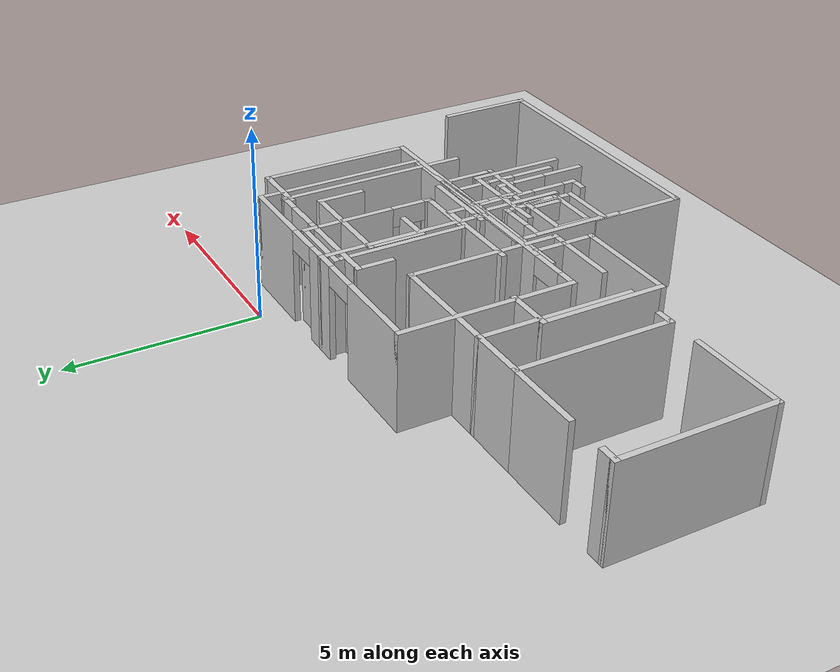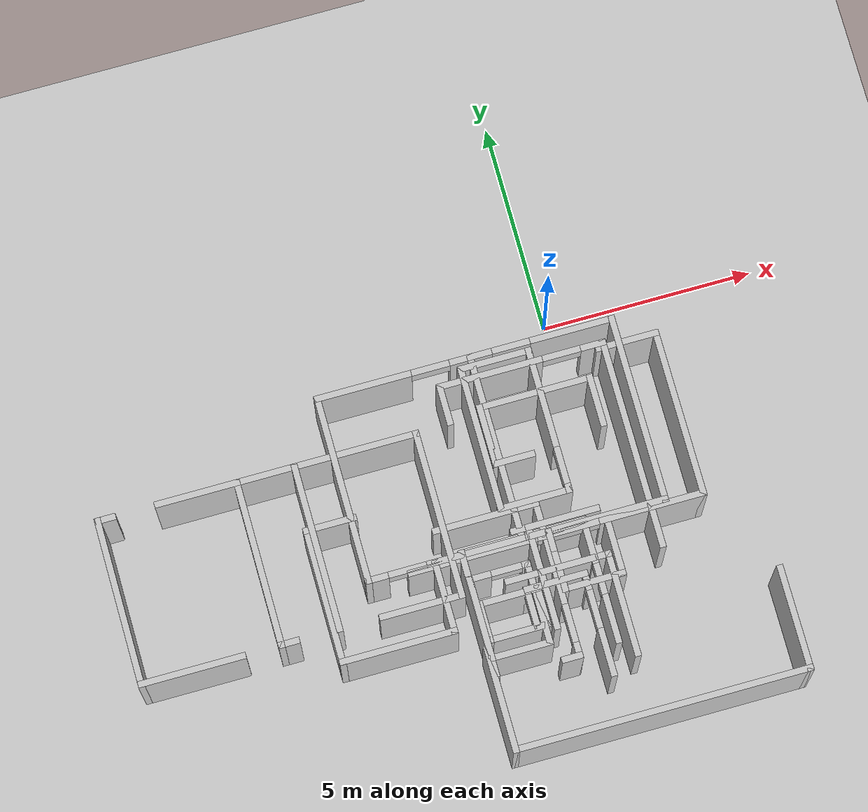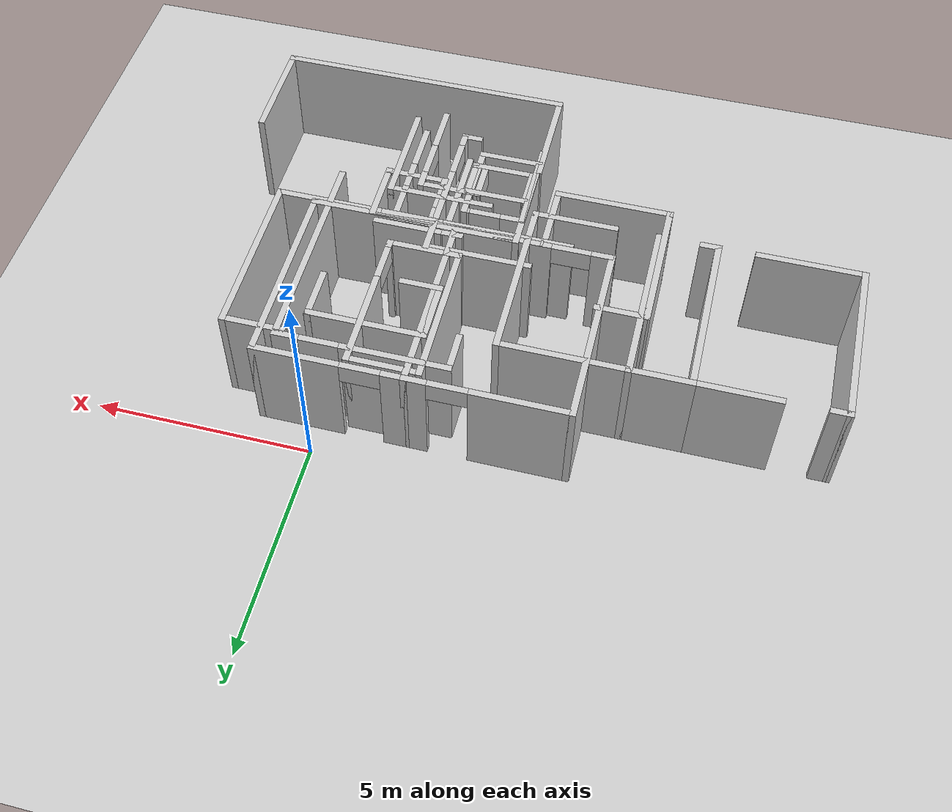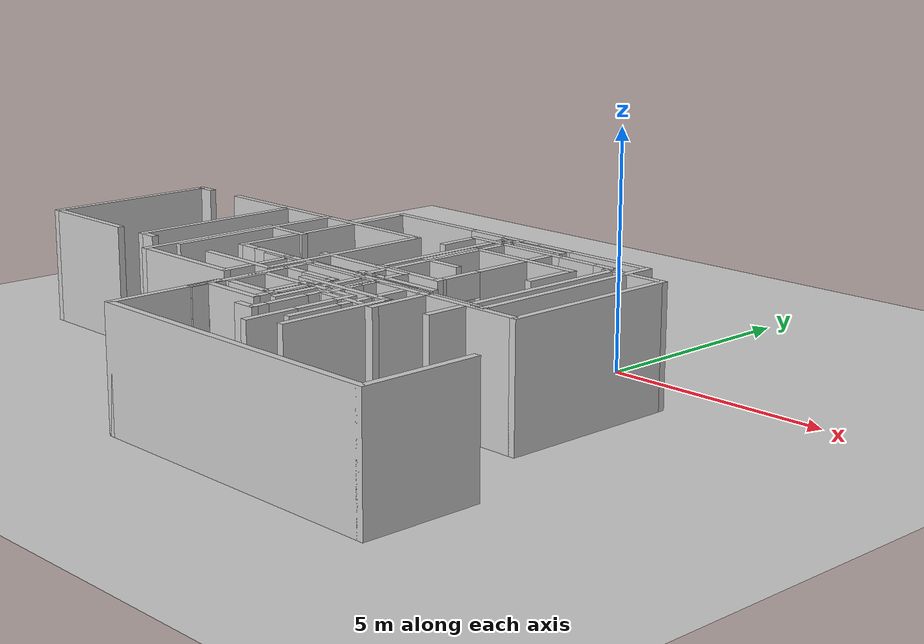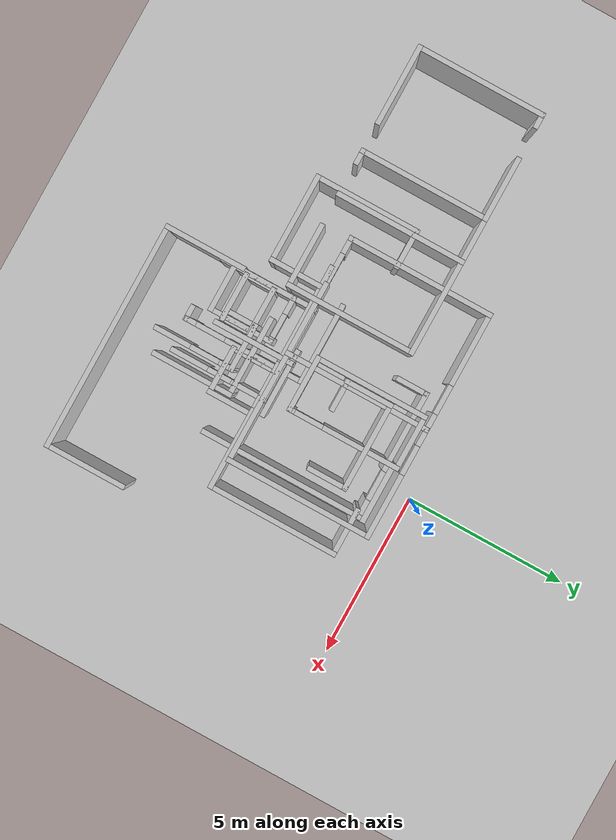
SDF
<sdf version='1.6'>
  <world name='default'>

    <!-- Plugins obrigatórios para Gazebo Harmonic (Ignition Gazebo 6) -->
    <plugin filename="gz-sim-physics-system"
            name="gz::sim::systems::Physics"/>
    <plugin filename="gz-sim-user-commands-system"
            name="gz::sim::systems::UserCommands"/>
    <plugin filename="gz-sim-scene-broadcaster-system"
            name="gz::sim::systems::SceneBroadcaster"/>
    <plugin filename="gz-sim-sensors-system"
            name="gz::sim::systems::Sensors">
      <render_engine>ogre2</render_engine>
    </plugin>
    <plugin filename="gz-sim-imu-system"
            name="gz::sim::systems::Imu"/>

    <!-- Ambient light para OGRE2 (sem isto a cena fica preta) -->
    <scene>
      <ambient>0.4 0.4 0.4 1</ambient>
      <background>0.7 0.7 0.7 1</background>
      <shadows>true</shadows>
    </scene>

    <light name='sun' type='directional'>
      <cast_shadows>1</cast_shadows>
      <pose>0 0 10 0 -0 0</pose>
      <diffuse>0.8 0.8 0.8 1</diffuse>
      <specular>0.1 0.1 0.1 1</specular>
      <attenuation>
        <range>1000</range>
        <constant>0.9</constant>
        <linear>0.01</linear>
        <quadratic>0.001</quadratic>
      </attenuation>
      <direction>-0.5 0.5 -1</direction>
    </light>
    <model name='ground_plane'>
      <static>1</static>
      <link name='link'>
        <collision name='collision'>
          <geometry>
            <plane>
              <normal>0 0 1</normal>
              <size>100 100</size>
            </plane>
          </geometry>
          <surface>
            <friction>
              <ode>
                <mu>100</mu>
                <mu2>50</mu2>
              </ode>
              <torsional>
                <ode/>
              </torsional>
            </friction>
            <contact>
              <ode/>
            </contact>
            <bounce/>
          </surface>
        </collision>
        <visual name='visual'>
          <cast_shadows>0</cast_shadows>
          <geometry>
            <plane>
              <normal>0 0 1</normal>
              <size>100 100</size>
            </plane>
          </geometry>
          <material>
            <diffuse>0.8 0.8 0.8 1</diffuse>
          </material>
        </visual>
        <self_collide>0</self_collide>
        <kinematic>0</kinematic>
        <gravity>1</gravity>
      </link>
    </model>
    <gravity>0 0 -9.8</gravity>
    <magnetic_field>6e-06 2.3e-05 -4.2e-05</magnetic_field>
    <atmosphere type='adiabatic'/>
    <physics name='default_physics' default='0' type='ode'>
      <max_step_size>0.001</max_step_size>
      <real_time_factor>1</real_time_factor>
      <real_time_update_rate>1000</real_time_update_rate>
    </physics>
    <scene>
      <ambient>0.4 0.4 0.4 1</ambient>
      <background>0.7 0.7 0.7 1</background>
      <shadows>1</shadows>
    </scene>
    <spherical_coordinates>
      <surface_model>EARTH_WGS84</surface_model>
      <latitude_deg>0</latitude_deg>
      <longitude_deg>0</longitude_deg>
      <elevation>0</elevation>
      <heading_deg>0</heading_deg>
    </spherical_coordinates>
    <model name='cma_escritorio'>
      <pose>-7.395 -4.04 0 0 -0 0</pose>
      <link name='Wall_11'>
        <collision name='Wall_11_Collision'>
          <geometry>
            <box>
              <size>2 0.15 2.5</size>
            </box>
          </geometry>
          <pose>0 0 1.25 0 -0 0</pose>
          <surface>
            <contact>
              <ode/>
            </contact>
            <bounce/>
            <friction>
              <torsional>
                <ode/>
              </torsional>
              <ode/>
            </friction>
          </surface>
        </collision>
        <visual name='Wall_11_Visual'>
          <pose>0 0 1.25 0 -0 0</pose>
          <geometry>
            <box>
              <size>2 0.15 2.5</size>
            </box>
          </geometry>
          <material>
            <diffuse>0.8 0.8 0.8 1</diffuse>
            <ambient>1 1 1 1</ambient>
          </material>
        </visual>
        <pose>-1.4 1.93 0 0 -0 3.14159</pose>
        <self_collide>0</self_collide>
        <kinematic>0</kinematic>
        <gravity>1</gravity>
      </link>
      <link name='Wall_2'>
        <collision name='Wall_2_Collision'>
          <geometry>
            <box>
              <size>4 0.15 2.5</size>
            </box>
          </geometry>
          <pose>0 0 1.25 0 -0 0</pose>
          <surface>
            <contact>
              <ode/>
            </contact>
            <bounce/>
            <friction>
              <torsional>
                <ode/>
              </torsional>
              <ode/>
            </friction>
          </surface>
        </collision>
        <visual name='Wall_2_Visual'>
          <pose>0 0 1.25 0 -0 0</pose>
          <geometry>
            <box>
              <size>4 0.15 2.5</size>
            </box>
          </geometry>
          <material>
            <diffuse>0.8 0.8 0.8 1</diffuse>
            <ambient>1 1 1 1</ambient>
          </material>
        </visual>
        <pose>0.875 0.005 0 0 -0 1.5708</pose>
        <self_collide>0</self_collide>
        <kinematic>0</kinematic>
        <gravity>1</gravity>
      </link>
      <link name='Wall_25'>
        <collision name='Wall_25_Collision'>
          <geometry>
            <box>
              <size>2.5 0.15 2.5</size>
            </box>
          </geometry>
          <pose>0 0 1.25 0 -0 0</pose>
          <surface>
            <contact>
              <ode/>
            </contact>
            <bounce/>
            <friction>
              <torsional>
                <ode/>
              </torsional>
              <ode/>
            </friction>
          </surface>
        </collision>
        <visual name='Wall_25_Visual'>
          <pose>0 0 1.25 0 -0 0</pose>
          <geometry>
            <box>
              <size>2.5 0.15 2.5</size>
            </box>
          </geometry>
          <material>
            <diffuse>0.8 0.8 0.8 1</diffuse>
            <ambient>1 1 1 1</ambient>
          </material>
        </visual>
        <pose>-2.55 -1.93 0 0 -0 3.14159</pose>
        <self_collide>0</self_collide>
        <kinematic>0</kinematic>
        <gravity>1</gravity>
      </link>
      <link name='Wall_26'>
        <collision name='Wall_26_Collision'>
          <geometry>
            <box>
              <size>4 0.15 2.5</size>
            </box>
          </geometry>
          <pose>0 0 1.25 0 -0 0</pose>
          <surface>
            <contact>
              <ode/>
            </contact>
            <bounce/>
            <friction>
              <torsional>
                <ode/>
              </torsional>
              <ode/>
            </friction>
          </surface>
        </collision>
        <visual name='Wall_26_Visual'>
          <pose>0 0 1.25 0 -0 0</pose>
          <geometry>
            <box>
              <size>4 0.15 2.5</size>
            </box>
          </geometry>
          <material>
            <diffuse>0.8 0.8 0.8 1</diffuse>
            <ambient>1 1 1 1</ambient>
          </material>
        </visual>
        <pose>-3.725 -0.005 0 0 -0 1.5708</pose>
        <self_collide>0</self_collide>
        <kinematic>0</kinematic>
        <gravity>1</gravity>
      </link>
      <link name='Wall_27'>
        <collision name='Wall_27_Collision'>
          <geometry>
            <box>
              <size>0.5 0.15 2.5</size>
            </box>
          </geometry>
          <pose>0 0 1.25 0 -0 0</pose>
          <surface>
            <contact>
              <ode/>
            </contact>
            <bounce/>
            <friction>
              <torsional>
                <ode/>
              </torsional>
              <ode/>
            </friction>
          </surface>
        </collision>
        <visual name='Wall_27_Visual'>
          <pose>0 0 1.25 0 -0 0</pose>
          <geometry>
            <box>
              <size>0.5 0.15 2.5</size>
            </box>
          </geometry>
          <material>
            <diffuse>0.8 0.8 0.8 1</diffuse>
            <ambient>1 1 1 1</ambient>
          </material>
        </visual>
        <pose>-3.55 1.92 0 0 -0 0</pose>
        <self_collide>0</self_collide>
        <kinematic>0</kinematic>
        <gravity>1</gravity>
      </link>
      <link name='Wall_3'>
        <collision name='Wall_3_Collision'>
          <geometry>
            <box>
              <size>3 0.15 2.5</size>
            </box>
          </geometry>
          <pose>0 0 1.25 0 -0 0</pose>
          <surface>
            <contact>
              <ode/>
            </contact>
            <bounce/>
            <friction>
              <torsional>
                <ode/>
              </torsional>
              <ode/>
            </friction>
          </surface>
        </collision>
        <visual name='Wall_3_Visual'>
          <pose>0 0 1.25 0 -0 0</pose>
          <geometry>
            <box>
              <size>3 0.15 2.5</size>
            </box>
          </geometry>
          <material>
            <diffuse>0.8 0.8 0.8 1</diffuse>
            <ambient>1 1 1 1</ambient>
          </material>
        </visual>
        <pose>2.3 1.93 0 0 -0 0</pose>
        <self_collide>0</self_collide>
        <kinematic>0</kinematic>
        <gravity>1</gravity>
      </link>
      <link name='Wall_4'>
        <collision name='Wall_4_Collision'>
          <geometry>
            <box>
              <size>4 0.15 2.5</size>
            </box>
          </geometry>
          <pose>0 0 1.25 0 -0 0</pose>
          <surface>
            <contact>
              <ode/>
            </contact>
            <bounce/>
            <friction>
              <torsional>
                <ode/>
              </torsional>
              <ode/>
            </friction>
          </surface>
        </collision>
        <visual name='Wall_4_Visual'>
          <pose>0 0 1.25 0 -0 0</pose>
          <geometry>
            <box>
              <size>4 0.15 2.5</size>
            </box>
          </geometry>
          <material>
            <diffuse>0.8 0.8 0.8 1</diffuse>
            <ambient>1 1 1 1</ambient>
          </material>
        </visual>
        <pose>3.725 0.005 0 0 0 -1.5708</pose>
        <self_collide>0</self_collide>
        <kinematic>0</kinematic>
        <gravity>1</gravity>
      </link>
      <link name='Wall_5'>
        <collision name='Wall_5_Collision'>
          <geometry>
            <box>
              <size>2 0.15 2.5</size>
            </box>
          </geometry>
          <pose>0 0 1.25 0 -0 0</pose>
          <surface>
            <contact>
              <ode/>
            </contact>
            <bounce/>
            <friction>
              <torsional>
                <ode/>
              </torsional>
              <ode/>
            </friction>
          </surface>
        </collision>
        <visual name='Wall_5_Visual'>
          <pose>0 0 1.25 0 -0 0</pose>
          <geometry>
            <box>
              <size>2 0.15 2.5</size>
            </box>
          </geometry>
          <material>
            <diffuse>0.8 0.8 0.8 1</diffuse>
            <ambient>1 1 1 1</ambient>
          </material>
        </visual>
        <pose>2.8 -1.92 0 0 -0 3.14159</pose>
        <self_collide>0</self_collide>
        <kinematic>0</kinematic>
        <gravity>1</gravity>
      </link>
      <link name='Wall_7'>
        <collision name='Wall_7_Collision'>
          <geometry>
            <box>
              <size>1.5 0.15 2.5</size>
            </box>
          </geometry>
          <pose>0 0 1.25 0 -0 0</pose>
          <surface>
            <contact>
              <ode/>
            </contact>
            <bounce/>
            <friction>
              <torsional>
                <ode/>
              </torsional>
              <ode/>
            </friction>
          </surface>
        </collision>
        <visual name='Wall_7_Visual'>
          <pose>0 0 1.25 0 -0 0</pose>
          <geometry>
            <box>
              <size>1.5 0.15 2.5</size>
            </box>
          </geometry>
          <material>
            <diffuse>0.8 0.8 0.8 1</diffuse>
            <ambient>1 1 1 1</ambient>
          </material>
        </visual>
        <pose>0.2 1.93 0 0 -0 3.14159</pose>
        <self_collide>0</self_collide>
        <kinematic>0</kinematic>
        <gravity>1</gravity>
      </link>
      <link name='Wall_8'>
        <collision name='Wall_8_Collision'>
          <geometry>
            <box>
              <size>4 0.15 2.5</size>
            </box>
          </geometry>
          <pose>0 0 1.25 0 -0 0</pose>
          <surface>
            <contact>
              <ode/>
            </contact>
            <bounce/>
            <friction>
              <torsional>
                <ode/>
              </torsional>
              <ode/>
            </friction>
          </surface>
        </collision>
        <visual name='Wall_8_Visual'>
          <pose>0 0 1.25 0 -0 0</pose>
          <geometry>
            <box>
              <size>4 0.15 2.5</size>
            </box>
          </geometry>
          <material>
            <diffuse>0.8 0.8 0.8 1</diffuse>
            <ambient>1 1 1 1</ambient>
          </material>
        </visual>
        <pose>-0.475 0.005 0 0 0 -1.5708</pose>
        <self_collide>0</self_collide>
        <kinematic>0</kinematic>
        <gravity>1</gravity>
      </link>
      <link name='Wall_9'>
        <collision name='Wall_9_Collision'>
          <geometry>
            <box>
              <size>0.5 0.15 2.5</size>
            </box>
          </geometry>
          <pose>0 0 1.25 0 -0 0</pose>
          <surface>
            <contact>
              <ode/>
            </contact>
            <bounce/>
            <friction>
              <torsional>
                <ode/>
              </torsional>
              <ode/>
            </friction>
          </surface>
        </collision>
        <visual name='Wall_9_Visual'>
          <pose>0 0 1.25 0 -0 0</pose>
          <geometry>
            <box>
              <size>0.5 0.15 2.5</size>
            </box>
          </geometry>
          <material>
            <diffuse>0.8 0.8 0.8 1</diffuse>
            <ambient>1 1 1 1</ambient>
          </material>
        </visual>
        <pose>-0.3 -1.92 0 0 -0 0</pose>
        <self_collide>0</self_collide>
        <kinematic>0</kinematic>
        <gravity>1</gravity>
      </link>
      <static>1</static>
    </model>
    <model name='cma_banheiro'>
      <pose>-0.82 -2.595 0 0 -0 0</pose>
      <link name='Wall_0'>
        <collision name='Wall_0_Collision'>
          <geometry>
            <box>
              <size>1 0.15 2.5</size>
            </box>
          </geometry>
          <pose>0 0 1.25 0 -0 0</pose>
          <surface>
            <contact>
              <ode/>
            </contact>
            <bounce/>
            <friction>
              <torsional>
                <ode/>
              </torsional>
              <ode/>
            </friction>
          </surface>
        </collision>
        <visual name='Wall_0_Visual'>
          <pose>0 0 1.25 0 -0 0</pose>
          <geometry>
            <box>
              <size>1 0.15 2.5</size>
            </box>
          </geometry>
          <material>
            <diffuse>0.8 0.8 0.8 1</diffuse>
            <ambient>1 1 1 1</ambient>
          </material>
        </visual>
        <pose>-0.875 -0.675 0 0 -0 3.14159</pose>
        <self_collide>0</self_collide>
        <kinematic>0</kinematic>
        <gravity>1</gravity>
      </link>
      <link name='Wall_1'>
        <collision name='Wall_1_Collision'>
          <geometry>
            <box>
              <size>1.5 0.15 2.5</size>
            </box>
          </geometry>
          <pose>0 0 1.25 0 -0 0</pose>
          <surface>
            <contact>
              <ode/>
            </contact>
            <bounce/>
            <friction>
              <torsional>
                <ode/>
              </torsional>
              <ode/>
            </friction>
          </surface>
        </collision>
        <visual name='Wall_1_Visual'>
          <pose>0 0 1.25 0 -0 0</pose>
          <geometry>
            <box>
              <size>1.5 0.15 2.5</size>
            </box>
          </geometry>
          <material>
            <diffuse>0.8 0.8 0.8 1</diffuse>
            <ambient>1 1 1 1</ambient>
          </material>
        </visual>
        <pose>-1.3 0 0 0 -0 1.5708</pose>
        <self_collide>0</self_collide>
        <kinematic>0</kinematic>
        <gravity>1</gravity>
      </link>
      <link name='Wall_2'>
        <collision name='Wall_2_Collision'>
          <geometry>
            <box>
              <size>2.75 0.15 2.5</size>
            </box>
          </geometry>
          <pose>0 0 1.25 0 -0 0</pose>
          <surface>
            <contact>
              <ode/>
            </contact>
            <bounce/>
            <friction>
              <torsional>
                <ode/>
              </torsional>
              <ode/>
            </friction>
          </surface>
        </collision>
        <visual name='Wall_2_Visual'>
          <pose>0 0 1.25 0 -0 0</pose>
          <geometry>
            <box>
              <size>2.75 0.15 2.5</size>
            </box>
          </geometry>
          <material>
            <diffuse>0.8 0.8 0.8 1</diffuse>
            <ambient>1 1 1 1</ambient>
          </material>
        </visual>
        <pose>0 0.675 0 0 -0 0</pose>
        <self_collide>0</self_collide>
        <kinematic>0</kinematic>
        <gravity>1</gravity>
      </link>
      <link name='Wall_4'>
        <collision name='Wall_4_Collision'>
          <geometry>
            <box>
              <size>1.25 0.15 2.5</size>
            </box>
          </geometry>
          <pose>0 0 1.25 0 -0 0</pose>
          <surface>
            <contact>
              <ode/>
            </contact>
            <bounce/>
            <friction>
              <torsional>
                <ode/>
              </torsional>
              <ode/>
            </friction>
          </surface>
        </collision>
        <visual name='Wall_4_Visual'>
          <pose>0 0 1.25 0 -0 0</pose>
          <geometry>
            <box>
              <size>1.25 0.15 2.5</size>
            </box>
          </geometry>
          <material>
            <diffuse>0.8 0.8 0.8 1</diffuse>
            <ambient>1 1 1 1</ambient>
          </material>
        </visual>
        <pose>1.3 0.125 0 0 0 -1.5708</pose>
        <self_collide>0</self_collide>
        <kinematic>0</kinematic>
        <gravity>1</gravity>
      </link>
      <static>1</static>
    </model>
    <model name='cma_varanda1'>
      <pose>-1.49 -2.615 0 0 -0 0</pose>
      <link name='Wall_0'>
        <pose>0.8 0 0 0 0 -1.5708</pose>
        <visual name='Wall_0_Visual_0'>
          <pose>-0.5525 0 1.25 0 -0 0</pose>
          <geometry>
            <box>
              <size>2.395 0.15 2.5</size>
            </box>
          </geometry>
          <material>
            <diffuse>0.8 0.8 0.8 1</diffuse>
            <ambient>1 1 1 1</ambient>
          </material>
        </visual>
        <collision name='Wall_0_Collision_0'>
          <geometry>
            <box>
              <size>2.395 0.15 2.5</size>
            </box>
          </geometry>
          <pose>-0.5525 0 1.25 0 -0 0</pose>
          <surface>
            <contact>
              <ode/>
            </contact>
            <bounce/>
            <friction>
              <torsional>
                <ode/>
              </torsional>
              <ode/>
            </friction>
          </surface>
        </collision>
        <visual name='Wall_0_Visual_1'>
          <pose>1.6375 0 1.25 0 -0 0</pose>
          <geometry>
            <box>
              <size>0.225 0.15 2.5</size>
            </box>
          </geometry>
          <material>
            <diffuse>0.8 0.8 0.8 1</diffuse>
            <ambient>1 1 1 1</ambient>
          </material>
        </visual>
        <collision name='Wall_0_Collision_1'>
          <geometry>
            <box>
              <size>0.225 0.15 2.5</size>
            </box>
          </geometry>
          <pose>1.6375 0 1.25 0 -0 0</pose>
          <surface>
            <contact>
              <ode/>
            </contact>
            <bounce/>
            <friction>
              <torsional>
                <ode/>
              </torsional>
              <ode/>
            </friction>
          </surface>
        </collision>
        <visual name='Wall_0_Visual_2'>
          <pose>1.085 0 2.25 0 -0 0</pose>
          <geometry>
            <box>
              <size>0.88 0.15 0.5</size>
            </box>
          </geometry>
          <material>
            <diffuse>0.8 0.8 0.8 1</diffuse>
            <ambient>1 1 1 1</ambient>
          </material>
        </visual>
        <collision name='Wall_0_Collision_2'>
          <geometry>
            <box>
              <size>0.88 0.15 0.5</size>
            </box>
          </geometry>
          <pose>1.085 0 2.25 0 -0 0</pose>
          <surface>
            <contact>
              <ode/>
            </contact>
            <bounce/>
            <friction>
              <torsional>
                <ode/>
              </torsional>
              <ode/>
            </friction>
          </surface>
        </collision>
        <self_collide>0</self_collide>
        <kinematic>0</kinematic>
        <gravity>1</gravity>
      </link>
      <link name='Wall_1'>
        <collision name='Wall_1_Collision'>
          <geometry>
            <box>
              <size>1.75 0.15 2.5</size>
            </box>
          </geometry>
          <pose>0 0 1.25 0 -0 0</pose>
          <surface>
            <contact>
              <ode/>
            </contact>
            <bounce/>
            <friction>
              <torsional>
                <ode/>
              </torsional>
              <ode/>
            </friction>
          </surface>
        </collision>
        <visual name='Wall_1_Visual'>
          <pose>0 0 1.25 0 -0 0</pose>
          <geometry>
            <box>
              <size>1.75 0.15 2.5</size>
            </box>
          </geometry>
          <material>
            <diffuse>0.8 0.8 0.8 1</diffuse>
            <ambient>1 1 1 1</ambient>
          </material>
        </visual>
        <pose>0 -1.675 0 0 -0 3.14159</pose>
        <self_collide>0</self_collide>
        <kinematic>0</kinematic>
        <gravity>1</gravity>
      </link>
      <link name='Wall_2'>
        <collision name='Wall_2_Collision'>
          <geometry>
            <box>
              <size>3.5 0.15 2.5</size>
            </box>
          </geometry>
          <pose>0 0 1.25 0 -0 0</pose>
          <surface>
            <contact>
              <ode/>
            </contact>
            <bounce/>
            <friction>
              <torsional>
                <ode/>
              </torsional>
              <ode/>
            </friction>
          </surface>
        </collision>
        <visual name='Wall_2_Visual'>
          <pose>0 0 1.25 0 -0 0</pose>
          <geometry>
            <box>
              <size>3.5 0.15 2.5</size>
            </box>
          </geometry>
          <material>
            <diffuse>0.8 0.8 0.8 1</diffuse>
            <ambient>1 1 1 1</ambient>
          </material>
        </visual>
        <pose>-0.8 0 0 0 -0 1.5708</pose>
        <self_collide>0</self_collide>
        <kinematic>0</kinematic>
        <gravity>1</gravity>
      </link>
      <link name='Wall_3'>
        <collision name='Wall_3_Collision'>
          <geometry>
            <box>
              <size>1.75 0.15 2.5</size>
            </box>
          </geometry>
          <pose>0 0 1.25 0 -0 0</pose>
          <surface>
            <contact>
              <ode/>
            </contact>
            <bounce/>
            <friction>
              <torsional>
                <ode/>
              </torsional>
              <ode/>
            </friction>
          </surface>
        </collision>
        <visual name='Wall_3_Visual'>
          <pose>0 0 1.25 0 -0 0</pose>
          <geometry>
            <box>
              <size>1.75 0.15 2.5</size>
            </box>
          </geometry>
          <material>
            <diffuse>0.8 0.8 0.8 1</diffuse>
            <ambient>1 1 1 1</ambient>
          </material>
        </visual>
        <pose>0 1.675 0 0 -0 0</pose>
        <self_collide>0</self_collide>
        <kinematic>0</kinematic>
        <gravity>1</gravity>
      </link>
      <static>1</static>
    </model>
    <model name='cma_quartos'>
      <pose>-2.655 -3.715 0 0 -0 0</pose>
      <link name='Wall_0'>
        <collision name='Wall_0_Collision'>
          <geometry>
            <box>
              <size>4.5 0.15 2.5</size>
            </box>
          </geometry>
          <pose>0 0 1.25 0 -0 0</pose>
          <surface>
            <contact>
              <ode/>
            </contact>
            <bounce/>
            <friction>
              <torsional>
                <ode/>
              </torsional>
              <ode/>
            </friction>
          </surface>
        </collision>
        <visual name='Wall_0_Visual'>
          <pose>0 0 1.25 0 -0 0</pose>
          <geometry>
            <box>
              <size>4.5 0.15 2.5</size>
            </box>
          </geometry>
          <material>
            <diffuse>0.8 0.8 0.8 1</diffuse>
            <ambient>1 1 1 1</ambient>
          </material>
        </visual>
        <pose>0.645 0.81 0 0 0 -1.5708</pose>
        <self_collide>0</self_collide>
        <kinematic>0</kinematic>
        <gravity>1</gravity>
      </link>
      <link name='Wall_1'>
        <pose>-1.155 -1.365 0 0 -0 3.14159</pose>
        <visual name='Wall_1_Visual_0'>
          <pose>-0.7225 0 1.25 0 -0 0</pose>
          <geometry>
            <box>
              <size>2.305 0.15 2.5</size>
            </box>
          </geometry>
          <material>
            <diffuse>0.8 0.8 0.8 1</diffuse>
            <ambient>1 1 1 1</ambient>
          </material>
        </visual>
        <collision name='Wall_1_Collision_0'>
          <geometry>
            <box>
              <size>2.305 0.15 2.5</size>
            </box>
          </geometry>
          <pose>-0.7225 0 1.25 0 -0 0</pose>
          <surface>
            <contact>
              <ode/>
            </contact>
            <bounce/>
            <friction>
              <torsional>
                <ode/>
              </torsional>
              <ode/>
            </friction>
          </surface>
        </collision>
        <visual name='Wall_1_Visual_1'>
          <pose>1.6025 0 1.25 0 -0 0</pose>
          <geometry>
            <box>
              <size>0.545 0.15 2.5</size>
            </box>
          </geometry>
          <material>
            <diffuse>0.8 0.8 0.8 1</diffuse>
            <ambient>1 1 1 1</ambient>
          </material>
        </visual>
        <collision name='Wall_1_Collision_1'>
          <geometry>
            <box>
              <size>0.545 0.15 2.5</size>
            </box>
          </geometry>
          <pose>1.6025 0 1.25 0 -0 0</pose>
          <surface>
            <contact>
              <ode/>
            </contact>
            <bounce/>
            <friction>
              <torsional>
                <ode/>
              </torsional>
              <ode/>
            </friction>
          </surface>
        </collision>
        <visual name='Wall_1_Visual_2'>
          <pose>0.88 0 2.25 0 -0 0</pose>
          <geometry>
            <box>
              <size>0.9 0.15 0.5</size>
            </box>
          </geometry>
          <material>
            <diffuse>0.8 0.8 0.8 1</diffuse>
            <ambient>1 1 1 1</ambient>
          </material>
        </visual>
        <collision name='Wall_1_Collision_2'>
          <geometry>
            <box>
              <size>0.9 0.15 0.5</size>
            </box>
          </geometry>
          <pose>0.88 0 2.25 0 -0 0</pose>
          <surface>
            <contact>
              <ode/>
            </contact>
            <bounce/>
            <friction>
              <torsional>
                <ode/>
              </torsional>
              <ode/>
            </friction>
          </surface>
        </collision>
        <self_collide>0</self_collide>
        <kinematic>0</kinematic>
        <gravity>1</gravity>
      </link>
      <link name='Wall_10'>
        <collision name='Wall_10_Collision'>
          <geometry>
            <box>
              <size>1.75 0.15 2.5</size>
            </box>
          </geometry>
          <pose>0 0 1.25 0 -0 0</pose>
          <surface>
            <contact>
              <ode/>
            </contact>
            <bounce/>
            <friction>
              <torsional>
                <ode/>
              </torsional>
              <ode/>
            </friction>
          </surface>
        </collision>
        <visual name='Wall_10_Visual'>
          <pose>0 0 1.25 0 -0 0</pose>
          <geometry>
            <box>
              <size>1.75 0.15 2.5</size>
            </box>
          </geometry>
          <material>
            <diffuse>0.8 0.8 0.8 1</diffuse>
            <ambient>1 1 1 1</ambient>
          </material>
        </visual>
        <pose>-1.395 -2.185 0 0 0 -1.5708</pose>
        <self_collide>0</self_collide>
        <kinematic>0</kinematic>
        <gravity>1</gravity>
      </link>
      <link name='Wall_11'>
        <collision name='Wall_11_Collision'>
          <geometry>
            <box>
              <size>2.75 0.15 2.5</size>
            </box>
          </geometry>
          <pose>0 0 1.25 0 -0 0</pose>
          <surface>
            <contact>
              <ode/>
            </contact>
            <bounce/>
            <friction>
              <torsional>
                <ode/>
              </torsional>
              <ode/>
            </friction>
          </surface>
        </collision>
        <visual name='Wall_11_Visual'>
          <pose>0 0 1.25 0 -0 0</pose>
          <geometry>
            <box>
              <size>2.75 0.15 2.5</size>
            </box>
          </geometry>
          <material>
            <diffuse>0.8 0.8 0.8 1</diffuse>
            <ambient>1 1 1 1</ambient>
          </material>
        </visual>
        <pose>-2.695 -2.985 0 0 -0 3.14159</pose>
        <self_collide>0</self_collide>
        <kinematic>0</kinematic>
        <gravity>1</gravity>
      </link>
      <link name='Wall_12'>
        <collision name='Wall_12_Collision'>
          <geometry>
            <box>
              <size>3.25 0.15 2.5</size>
            </box>
          </geometry>
          <pose>0 0 1.25 0 -0 0</pose>
          <surface>
            <contact>
              <ode/>
            </contact>
            <bounce/>
            <friction>
              <torsional>
                <ode/>
              </torsional>
              <ode/>
            </friction>
          </surface>
        </collision>
        <visual name='Wall_12_Visual'>
          <pose>0 0 1.25 0 -0 0</pose>
          <geometry>
            <box>
              <size>3.25 0.15 2.5</size>
            </box>
          </geometry>
          <material>
            <diffuse>0.8 0.8 0.8 1</diffuse>
            <ambient>1 1 1 1</ambient>
          </material>
        </visual>
        <pose>-3.995 -1.435 0 0 -0 1.5708</pose>
        <self_collide>0</self_collide>
        <kinematic>0</kinematic>
        <gravity>1</gravity>
      </link>
      <link name='Wall_13'>
        <collision name='Wall_13_Collision'>
          <geometry>
            <box>
              <size>1.25 0.15 2.5</size>
            </box>
          </geometry>
          <pose>0 0 1.25 0 -0 0</pose>
          <surface>
            <contact>
              <ode/>
            </contact>
            <bounce/>
            <friction>
              <torsional>
                <ode/>
              </torsional>
              <ode/>
            </friction>
          </surface>
        </collision>
        <visual name='Wall_13_Visual'>
          <pose>0 0 1.25 0 -0 0</pose>
          <geometry>
            <box>
              <size>1.25 0.15 2.5</size>
            </box>
          </geometry>
          <material>
            <diffuse>0.8 0.8 0.8 1</diffuse>
            <ambient>1 1 1 1</ambient>
          </material>
        </visual>
        <pose>-3.445 0.115 0 0 -0 0</pose>
        <self_collide>0</self_collide>
        <kinematic>0</kinematic>
        <gravity>1</gravity>
      </link>
      <link name='Wall_2'>
        <collision name='Wall_2_Collision'>
          <geometry>
            <box>
              <size>4.5 0.15 2.5</size>
            </box>
          </geometry>
          <pose>0 0 1.25 0 -0 0</pose>
          <surface>
            <contact>
              <ode/>
            </contact>
            <bounce/>
            <friction>
              <torsional>
                <ode/>
              </torsional>
              <ode/>
            </friction>
          </surface>
        </collision>
        <visual name='Wall_2_Visual'>
          <pose>0 0 1.25 0 -0 0</pose>
          <geometry>
            <box>
              <size>4.5 0.15 2.5</size>
            </box>
          </geometry>
          <material>
            <diffuse>0.8 0.8 0.8 1</diffuse>
            <ambient>1 1 1 1</ambient>
          </material>
        </visual>
        <pose>-2.955 0.81 0 0 -0 1.5708</pose>
        <self_collide>0</self_collide>
        <kinematic>0</kinematic>
        <gravity>1</gravity>
      </link>
      <link name='Wall_3'>
        <pose>-1.155 2.985 0 0 -0 0</pose>
        <visual name='Wall_3_Visual_0'>
          <pose>-0.7325 0 1.25 0 -0 0</pose>
          <geometry>
            <box>
              <size>2.285 0.15 2.5</size>
            </box>
          </geometry>
          <material>
            <diffuse>0.8 0.8 0.8 1</diffuse>
            <ambient>1 1 1 1</ambient>
          </material>
        </visual>
        <collision name='Wall_3_Collision_0'>
          <geometry>
            <box>
              <size>2.285 0.15 2.5</size>
            </box>
          </geometry>
          <pose>-0.7325 0 1.25 0 -0 0</pose>
          <surface>
            <contact>
              <ode/>
            </contact>
            <bounce/>
            <friction>
              <torsional>
                <ode/>
              </torsional>
              <ode/>
            </friction>
          </surface>
        </collision>
        <visual name='Wall_3_Visual_1'>
          <pose>1.5925 0 1.25 0 -0 0</pose>
          <geometry>
            <box>
              <size>0.565 0.15 2.5</size>
            </box>
          </geometry>
          <material>
            <diffuse>0.8 0.8 0.8 1</diffuse>
            <ambient>1 1 1 1</ambient>
          </material>
        </visual>
        <collision name='Wall_3_Collision_1'>
          <geometry>
            <box>
              <size>0.565 0.15 2.5</size>
            </box>
          </geometry>
          <pose>1.5925 0 1.25 0 -0 0</pose>
          <surface>
            <contact>
              <ode/>
            </contact>
            <bounce/>
            <friction>
              <torsional>
                <ode/>
              </torsional>
              <ode/>
            </friction>
          </surface>
        </collision>
        <visual name='Wall_3_Visual_2'>
          <pose>0.86 0 2.25 0 -0 0</pose>
          <geometry>
            <box>
              <size>0.9 0.15 0.5</size>
            </box>
          </geometry>
          <material>
            <diffuse>0.8 0.8 0.8 1</diffuse>
            <ambient>1 1 1 1</ambient>
          </material>
        </visual>
        <collision name='Wall_3_Collision_2'>
          <geometry>
            <box>
              <size>0.9 0.15 0.5</size>
            </box>
          </geometry>
          <pose>0.86 0 2.25 0 -0 0</pose>
          <surface>
            <contact>
              <ode/>
            </contact>
            <bounce/>
            <friction>
              <torsional>
                <ode/>
              </torsional>
              <ode/>
            </friction>
          </surface>
        </collision>
        <self_collide>0</self_collide>
        <kinematic>0</kinematic>
        <gravity>1</gravity>
      </link>
      <link name='Wall_6'>
        <pose>2.32 2.985 0 0 -0 0</pose>
        <visual name='Wall_6_Visual_0'>
          <pose>-1.4575 0 1.25 0 -0 0</pose>
          <geometry>
            <box>
              <size>0.585 0.15 2.5</size>
            </box>
          </geometry>
          <material>
            <diffuse>0.8 0.8 0.8 1</diffuse>
            <ambient>1 1 1 1</ambient>
          </material>
        </visual>
        <collision name='Wall_6_Collision_0'>
          <geometry>
            <box>
              <size>0.585 0.15 2.5</size>
            </box>
          </geometry>
          <pose>-1.4575 0 1.25 0 -0 0</pose>
          <surface>
            <contact>
              <ode/>
            </contact>
            <bounce/>
            <friction>
              <torsional>
                <ode/>
              </torsional>
              <ode/>
            </friction>
          </surface>
        </collision>
        <visual name='Wall_6_Visual_1'>
          <pose>0.7425 0 1.25 0 -0 0</pose>
          <geometry>
            <box>
              <size>2.015 0.15 2.5</size>
            </box>
          </geometry>
          <material>
            <diffuse>0.8 0.8 0.8 1</diffuse>
            <ambient>1 1 1 1</ambient>
          </material>
        </visual>
        <collision name='Wall_6_Collision_1'>
          <geometry>
            <box>
              <size>2.015 0.15 2.5</size>
            </box>
          </geometry>
          <pose>0.7425 0 1.25 0 -0 0</pose>
          <surface>
            <contact>
              <ode/>
            </contact>
            <bounce/>
            <friction>
              <torsional>
                <ode/>
              </torsional>
              <ode/>
            </friction>
          </surface>
        </collision>
        <visual name='Wall_6_Visual_2'>
          <pose>-0.715 0 2.25 0 -0 0</pose>
          <geometry>
            <box>
              <size>0.9 0.15 0.5</size>
            </box>
          </geometry>
          <material>
            <diffuse>0.8 0.8 0.8 1</diffuse>
            <ambient>1 1 1 1</ambient>
          </material>
        </visual>
        <collision name='Wall_6_Collision_2'>
          <geometry>
            <box>
              <size>0.9 0.15 0.5</size>
            </box>
          </geometry>
          <pose>-0.715 0 2.25 0 -0 0</pose>
          <surface>
            <contact>
              <ode/>
            </contact>
            <bounce/>
            <friction>
              <torsional>
                <ode/>
              </torsional>
              <ode/>
            </friction>
          </surface>
        </collision>
        <self_collide>0</self_collide>
        <kinematic>0</kinematic>
        <gravity>1</gravity>
      </link>
      <link name='Wall_7'>
        <collision name='Wall_7_Collision'>
          <geometry>
            <box>
              <size>4.5 0.15 2.5</size>
            </box>
          </geometry>
          <pose>0 0 1.25 0 -0 0</pose>
          <surface>
            <contact>
              <ode/>
            </contact>
            <bounce/>
            <friction>
              <torsional>
                <ode/>
              </torsional>
              <ode/>
            </friction>
          </surface>
        </collision>
        <visual name='Wall_7_Visual'>
          <pose>0 0 1.25 0 -0 0</pose>
          <geometry>
            <box>
              <size>4.5 0.15 2.5</size>
            </box>
          </geometry>
          <material>
            <diffuse>0.8 0.8 0.8 1</diffuse>
            <ambient>1 1 1 1</ambient>
          </material>
        </visual>
        <pose>3.995 0.81 0 0 0 -1.5708</pose>
        <self_collide>0</self_collide>
        <kinematic>0</kinematic>
        <gravity>1</gravity>
      </link>
      <link name='Wall_8'>
        <collision name='Wall_8_Collision'>
          <geometry>
            <box>
              <size>3.5 0.15 2.5</size>
            </box>
          </geometry>
          <pose>0 0 1.25 0 -0 0</pose>
          <surface>
            <contact>
              <ode/>
            </contact>
            <bounce/>
            <friction>
              <torsional>
                <ode/>
              </torsional>
              <ode/>
            </friction>
          </surface>
        </collision>
        <visual name='Wall_8_Visual'>
          <pose>0 0 1.25 0 -0 0</pose>
          <geometry>
            <box>
              <size>3.5 0.15 2.5</size>
            </box>
          </geometry>
          <material>
            <diffuse>0.8 0.8 0.8 1</diffuse>
            <ambient>1 1 1 1</ambient>
          </material>
        </visual>
        <pose>2.32 -1.365 0 0 -0 3.14159</pose>
        <self_collide>0</self_collide>
        <kinematic>0</kinematic>
        <gravity>1</gravity>
      </link>
      <static>1</static>
    </model>
    <model name='cma_parede_t'>
      <pose>-1.185 -6.045 0 0 -0 0</pose>
      <link name='Wall_15'>
        <collision name='Wall_15_Collision'>
          <geometry>
            <box>
              <size>2.5 0.15 2.5</size>
            </box>
          </geometry>
          <pose>0 0 1.25 0 -0 0</pose>
          <surface>
            <contact>
              <ode/>
            </contact>
            <bounce/>
            <friction>
              <torsional>
                <ode/>
              </torsional>
              <ode/>
            </friction>
          </surface>
        </collision>
        <visual name='Wall_15_Visual'>
          <pose>0 0 1.25 0 -0 0</pose>
          <geometry>
            <box>
              <size>2.5 0.15 2.5</size>
            </box>
          </geometry>
          <material>
            <diffuse>0.8 0.8 0.8 1</diffuse>
            <ambient>1 1 1 1</ambient>
          </material>
        </visual>
        <pose>-0.625 0 0 0 -0 1.5708</pose>
        <self_collide>0</self_collide>
        <kinematic>0</kinematic>
        <gravity>1</gravity>
      </link>
      <link name='Wall_16'>
        <collision name='Wall_16_Collision'>
          <geometry>
            <box>
              <size>0.5 0.15 2.5</size>
            </box>
          </geometry>
          <pose>0 0 1.25 0 -0 0</pose>
          <surface>
            <contact>
              <ode/>
            </contact>
            <bounce/>
            <friction>
              <torsional>
                <ode/>
              </torsional>
              <ode/>
            </friction>
          </surface>
        </collision>
        <visual name='Wall_16_Visual'>
          <pose>0 0 1.25 0 -0 0</pose>
          <geometry>
            <box>
              <size>0.5 0.15 2.5</size>
            </box>
          </geometry>
          <material>
            <diffuse>0.8 0.8 0.8 1</diffuse>
            <ambient>1 1 1 1</ambient>
          </material>
        </visual>
        <pose>-0.8 1.175 0 0 -0 3.14159</pose>
        <self_collide>0</self_collide>
        <kinematic>0</kinematic>
        <gravity>1</gravity>
      </link>
      <link name='Wall_18'>
        <collision name='Wall_18_Collision'>
          <geometry>
            <box>
              <size>1.75 0.15 2.5</size>
            </box>
          </geometry>
          <pose>0 0 1.25 0 -0 0</pose>
          <surface>
            <contact>
              <ode/>
            </contact>
            <bounce/>
            <friction>
              <torsional>
                <ode/>
              </torsional>
              <ode/>
            </friction>
          </surface>
        </collision>
        <visual name='Wall_18_Visual'>
          <pose>0 0 1.25 0 -0 0</pose>
          <geometry>
            <box>
              <size>1.75 0.15 2.5</size>
            </box>
          </geometry>
          <material>
            <diffuse>0.8 0.8 0.8 1</diffuse>
            <ambient>1 1 1 1</ambient>
          </material>
        </visual>
        <pose>0.175 1.175 0 0 -0 0</pose>
        <self_collide>0</self_collide>
        <kinematic>0</kinematic>
        <gravity>1</gravity>
      </link>
      <static>1</static>
    </model>
    <model name='cma_parede_L'>
      <pose>-1.215 -3.245 0 0 -0 0</pose>
      <link name='Wall_0'>
        <pose>0 -1.925 0 0 -0 0</pose>
        <visual name='Wall_0_Visual_0'>
          <pose>-1.985 0 1.25 0 -0 0</pose>
          <geometry>
            <box>
              <size>3.03 0.15 2.5</size>
            </box>
          </geometry>
          <material>
            <diffuse>0.8 0.8 0.8 1</diffuse>
            <ambient>1 1 1 1</ambient>
          </material>
        </visual>
        <collision name='Wall_0_Collision_0'>
          <geometry>
            <box>
              <size>3.03 0.15 2.5</size>
            </box>
          </geometry>
          <pose>-1.985 0 1.25 0 -0 0</pose>
          <surface>
            <contact>
              <ode/>
            </contact>
            <bounce/>
            <friction>
              <torsional>
                <ode/>
              </torsional>
              <ode/>
            </friction>
          </surface>
        </collision>
        <visual name='Wall_0_Visual_1'>
          <pose>2.24 0 1.25 0 -0 0</pose>
          <geometry>
            <box>
              <size>2.52 0.15 2.5</size>
            </box>
          </geometry>
          <material>
            <diffuse>0.8 0.8 0.8 1</diffuse>
            <ambient>1 1 1 1</ambient>
          </material>
        </visual>
        <collision name='Wall_0_Collision_1'>
          <geometry>
            <box>
              <size>2.52 0.15 2.5</size>
            </box>
          </geometry>
          <pose>2.24 0 1.25 0 -0 0</pose>
          <surface>
            <contact>
              <ode/>
            </contact>
            <bounce/>
            <friction>
              <torsional>
                <ode/>
              </torsional>
              <ode/>
            </friction>
          </surface>
        </collision>
        <visual name='Wall_0_Visual_2'>
          <pose>0.255 0 2.25 0 -0 0</pose>
          <geometry>
            <box>
              <size>1.45 0.15 0.5</size>
            </box>
          </geometry>
          <material>
            <diffuse>0.8 0.8 0.8 1</diffuse>
            <ambient>1 1 1 1</ambient>
          </material>
        </visual>
        <collision name='Wall_0_Collision_2'>
          <geometry>
            <box>
              <size>1.45 0.15 0.5</size>
            </box>
          </geometry>
          <pose>0.255 0 2.25 0 -0 0</pose>
          <surface>
            <contact>
              <ode/>
            </contact>
            <bounce/>
            <friction>
              <torsional>
                <ode/>
              </torsional>
              <ode/>
            </friction>
          </surface>
        </collision>
        <self_collide>0</self_collide>
        <kinematic>0</kinematic>
        <gravity>1</gravity>
      </link>
      <link name='Wall_1'>
        <collision name='Wall_1_Collision'>
          <geometry>
            <box>
              <size>4 0.15 2.5</size>
            </box>
          </geometry>
          <pose>0 0 1.25 0 -0 0</pose>
          <surface>
            <contact>
              <ode/>
            </contact>
            <bounce/>
            <friction>
              <torsional>
                <ode/>
              </torsional>
              <ode/>
            </friction>
          </surface>
        </collision>
        <visual name='Wall_1_Visual'>
          <pose>0 0 1.25 0 -0 0</pose>
          <geometry>
            <box>
              <size>4 0.15 2.5</size>
            </box>
          </geometry>
          <material>
            <diffuse>0.8 0.8 0.8 1</diffuse>
            <ambient>1 1 1 1</ambient>
          </material>
        </visual>
        <pose>3.425 0 0 0 -0 1.5708</pose>
        <self_collide>0</self_collide>
        <kinematic>0</kinematic>
        <gravity>1</gravity>
      </link>
      <link name='Wall_2'>
        <collision name='Wall_2_Collision'>
          <geometry>
            <box>
              <size>1.5 0.15 2.5</size>
            </box>
          </geometry>
          <pose>0 0 1.25 0 -0 0</pose>
          <surface>
            <contact>
              <ode/>
            </contact>
            <bounce/>
            <friction>
              <torsional>
                <ode/>
              </torsional>
              <ode/>
            </friction>
          </surface>
        </collision>
        <visual name='Wall_2_Visual'>
          <pose>0 0 1.25 0 -0 0</pose>
          <geometry>
            <box>
              <size>1.5 0.15 2.5</size>
            </box>
          </geometry>
          <material>
            <diffuse>0.8 0.8 0.8 1</diffuse>
            <ambient>1 1 1 1</ambient>
          </material>
        </visual>
        <pose>2.75 1.925 0 0 -0 3.14159</pose>
        <self_collide>0</self_collide>
        <kinematic>0</kinematic>
        <gravity>1</gravity>
      </link>
      <static>1</static>
    </model>
    <model name='cma_lavabo'>
      <pose>-0.725 -5.775 0 0 -0 0</pose>
      <link name='Wall_4'>
        <pose>-0.675 0 0 0 -0 1.5708</pose>
        <visual name='Wall_4_Visual_0'>
          <pose>-0.635 0 1.25 0 -0 0</pose>
          <geometry>
            <box>
              <size>0.23 0.15 2.5</size>
            </box>
          </geometry>
          <material>
            <diffuse>0.8 0.8 0.8 1</diffuse>
            <ambient>1 1 1 1</ambient>
          </material>
        </visual>
        <collision name='Wall_4_Collision_0'>
          <geometry>
            <box>
              <size>0.23 0.15 2.5</size>
            </box>
          </geometry>
          <pose>-0.635 0 1.25 0 -0 0</pose>
          <surface>
            <contact>
              <ode/>
            </contact>
            <bounce/>
            <friction>
              <torsional>
                <ode/>
              </torsional>
              <ode/>
            </friction>
          </surface>
        </collision>
        <visual name='Wall_4_Visual_1'>
          <pose>0.48 0 1.25 0 -0 0</pose>
          <geometry>
            <box>
              <size>0.54 0.15 2.5</size>
            </box>
          </geometry>
          <material>
            <diffuse>0.8 0.8 0.8 1</diffuse>
            <ambient>1 1 1 1</ambient>
          </material>
        </visual>
        <collision name='Wall_4_Collision_1'>
          <geometry>
            <box>
              <size>0.54 0.15 2.5</size>
            </box>
          </geometry>
          <pose>0.48 0 1.25 0 -0 0</pose>
          <surface>
            <contact>
              <ode/>
            </contact>
            <bounce/>
            <friction>
              <torsional>
                <ode/>
              </torsional>
              <ode/>
            </friction>
          </surface>
        </collision>
        <visual name='Wall_4_Visual_2'>
          <pose>-0.155 0 2.25 0 -0 0</pose>
          <geometry>
            <box>
              <size>0.73 0.15 0.5</size>
            </box>
          </geometry>
          <material>
            <diffuse>0.8 0.8 0.8 1</diffuse>
            <ambient>1 1 1 1</ambient>
          </material>
        </visual>
        <collision name='Wall_4_Collision_2'>
          <geometry>
            <box>
              <size>0.73 0.15 0.5</size>
            </box>
          </geometry>
          <pose>-0.155 0 2.25 0 -0 0</pose>
          <surface>
            <contact>
              <ode/>
            </contact>
            <bounce/>
            <friction>
              <torsional>
                <ode/>
              </torsional>
              <ode/>
            </friction>
          </surface>
        </collision>
        <self_collide>0</self_collide>
        <kinematic>0</kinematic>
        <gravity>1</gravity>
      </link>
      <link name='Wall_5'>
        <collision name='Wall_5_Collision'>
          <geometry>
            <box>
              <size>1.5 0.15 2.5</size>
            </box>
          </geometry>
          <pose>0 0 1.25 0 -0 0</pose>
          <surface>
            <contact>
              <ode/>
            </contact>
            <bounce/>
            <friction>
              <torsional>
                <ode/>
              </torsional>
              <ode/>
            </friction>
          </surface>
        </collision>
        <visual name='Wall_5_Visual'>
          <pose>0 0 1.25 0 -0 0</pose>
          <geometry>
            <box>
              <size>1.5 0.15 2.5</size>
            </box>
          </geometry>
          <material>
            <diffuse>0.8 0.8 0.8 1</diffuse>
            <ambient>1 1 1 1</ambient>
          </material>
        </visual>
        <pose>0 0.675 0 0 -0 0</pose>
        <self_collide>0</self_collide>
        <kinematic>0</kinematic>
        <gravity>1</gravity>
      </link>
      <link name='Wall_6'>
        <collision name='Wall_6_Collision'>
          <geometry>
            <box>
              <size>1.5 0.15 2.5</size>
            </box>
          </geometry>
          <pose>0 0 1.25 0 -0 0</pose>
          <surface>
            <contact>
              <ode/>
            </contact>
            <bounce/>
            <friction>
              <torsional>
                <ode/>
              </torsional>
              <ode/>
            </friction>
          </surface>
        </collision>
        <visual name='Wall_6_Visual'>
          <pose>0 0 1.25 0 -0 0</pose>
          <geometry>
            <box>
              <size>1.5 0.15 2.5</size>
            </box>
          </geometry>
          <material>
            <diffuse>0.8 0.8 0.8 1</diffuse>
            <ambient>1 1 1 1</ambient>
          </material>
        </visual>
        <pose>0.675 0 0 0 0 -1.5708</pose>
        <self_collide>0</self_collide>
        <kinematic>0</kinematic>
        <gravity>1</gravity>
      </link>
      <link name='Wall_7'>
        <collision name='Wall_7_Collision'>
          <geometry>
            <box>
              <size>1.5 0.15 2.5</size>
            </box>
          </geometry>
          <pose>0 0 1.25 0 -0 0</pose>
          <surface>
            <contact>
              <ode/>
            </contact>
            <bounce/>
            <friction>
              <torsional>
                <ode/>
              </torsional>
              <ode/>
            </friction>
          </surface>
        </collision>
        <visual name='Wall_7_Visual'>
          <pose>0 0 1.25 0 -0 0</pose>
          <geometry>
            <box>
              <size>1.5 0.15 2.5</size>
            </box>
          </geometry>
          <material>
            <diffuse>0.8 0.8 0.8 1</diffuse>
            <ambient>1 1 1 1</ambient>
          </material>
        </visual>
        <pose>0 -0.675 0 0 -0 3.14159</pose>
        <self_collide>0</self_collide>
        <kinematic>0</kinematic>
        <gravity>1</gravity>
      </link>
      <static>1</static>
    </model>
    <model name='cma_L2'>
      <pose>-1.415 -7.115 0 0 -0 0</pose>
      <link name='Wall_10'>
        <collision name='Wall_10_Collision'>
          <geometry>
            <box>
              <size>2.5 0.15 2.5</size>
            </box>
          </geometry>
          <pose>0 0 1.25 0 -0 0</pose>
          <surface>
            <contact>
              <ode/>
            </contact>
            <bounce/>
            <friction>
              <torsional>
                <ode/>
              </torsional>
              <ode/>
            </friction>
          </surface>
        </collision>
        <visual name='Wall_10_Visual'>
          <pose>0 0 1.25 0 -0 0</pose>
          <geometry>
            <box>
              <size>2.5 0.15 2.5</size>
            </box>
          </geometry>
          <material>
            <diffuse>0.8 0.8 0.8 1</diffuse>
            <ambient>1 1 1 1</ambient>
          </material>
        </visual>
        <pose>1.175 0 0 0 0 -1.5708</pose>
        <self_collide>0</self_collide>
        <kinematic>0</kinematic>
        <gravity>1</gravity>
      </link>
      <link name='Wall_9'>
        <collision name='Wall_9_Collision'>
          <geometry>
            <box>
              <size>2.5 0.15 2.5</size>
            </box>
          </geometry>
          <pose>0 0 1.25 0 -0 0</pose>
          <surface>
            <contact>
              <ode/>
            </contact>
            <bounce/>
            <friction>
              <torsional>
                <ode/>
              </torsional>
              <ode/>
            </friction>
          </surface>
        </collision>
        <visual name='Wall_9_Visual'>
          <pose>0 0 1.25 0 -0 0</pose>
          <geometry>
            <box>
              <size>2.5 0.15 2.5</size>
            </box>
          </geometry>
          <material>
            <diffuse>0.8 0.8 0.8 1</diffuse>
            <ambient>1 1 1 1</ambient>
          </material>
        </visual>
        <pose>0 1.175 0 0 -0 0</pose>
        <self_collide>0</self_collide>
        <kinematic>0</kinematic>
        <gravity>1</gravity>
      </link>
      <static>1</static>
    </model>
    <model name='cma_L3'>
      <pose>-1.555 -7.405 0 0 -0 0</pose>
      <link name='Wall_12'>
        <pose>-0.675 0.75 0 0 -0 1.5708</pose>
        <visual name='Wall_12_Visual_0'>
          <pose>-0.46 0 1.25 0 -0 0</pose>
          <geometry>
            <box>
              <size>0.08 0.15 2.5</size>
            </box>
          </geometry>
          <material>
            <diffuse>0.8 0.8 0.8 1</diffuse>
            <ambient>1 1 1 1</ambient>
          </material>
        </visual>
        <collision name='Wall_12_Collision_0'>
          <geometry>
            <box>
              <size>0.08 0.15 2.5</size>
            </box>
          </geometry>
          <pose>-0.46 0 1.25 0 -0 0</pose>
          <surface>
            <contact>
              <ode/>
            </contact>
            <bounce/>
            <friction>
              <torsional>
                <ode/>
              </torsional>
              <ode/>
            </friction>
          </surface>
        </collision>
        <visual name='Wall_12_Visual_1'>
          <pose>0.405 0 1.25 0 -0 0</pose>
          <geometry>
            <box>
              <size>0.19 0.15 2.5</size>
            </box>
          </geometry>
          <material>
            <diffuse>0.8 0.8 0.8 1</diffuse>
            <ambient>1 1 1 1</ambient>
          </material>
        </visual>
        <collision name='Wall_12_Collision_1'>
          <geometry>
            <box>
              <size>0.19 0.15 2.5</size>
            </box>
          </geometry>
          <pose>0.405 0 1.25 0 -0 0</pose>
          <surface>
            <contact>
              <ode/>
            </contact>
            <bounce/>
            <friction>
              <torsional>
                <ode/>
              </torsional>
              <ode/>
            </friction>
          </surface>
        </collision>
        <visual name='Wall_12_Visual_2'>
          <pose>-0.055 0 2.25 0 -0 0</pose>
          <geometry>
            <box>
              <size>0.73 0.15 0.5</size>
            </box>
          </geometry>
          <material>
            <diffuse>0.8 0.8 0.8 1</diffuse>
            <ambient>1 1 1 1</ambient>
          </material>
        </visual>
        <collision name='Wall_12_Collision_2'>
          <geometry>
            <box>
              <size>0.73 0.15 0.5</size>
            </box>
          </geometry>
          <pose>-0.055 0 2.25 0 -0 0</pose>
          <surface>
            <contact>
              <ode/>
            </contact>
            <bounce/>
            <friction>
              <torsional>
                <ode/>
              </torsional>
              <ode/>
            </friction>
          </surface>
        </collision>
        <self_collide>0</self_collide>
        <kinematic>0</kinematic>
        <gravity>1</gravity>
      </link>
      <link name='Wall_13'>
        <collision name='Wall_13_Collision'>
          <geometry>
            <box>
              <size>1.5 0.15 2.5</size>
            </box>
          </geometry>
          <pose>0 0 1.25 0 -0 0</pose>
          <surface>
            <contact>
              <ode/>
            </contact>
            <bounce/>
            <friction>
              <torsional>
                <ode/>
              </torsional>
              <ode/>
            </friction>
          </surface>
        </collision>
        <visual name='Wall_13_Visual'>
          <pose>0 0 1.25 0 -0 0</pose>
          <geometry>
            <box>
              <size>1.5 0.15 2.5</size>
            </box>
          </geometry>
          <material>
            <diffuse>0.8 0.8 0.8 1</diffuse>
            <ambient>1 1 1 1</ambient>
          </material>
        </visual>
        <pose>0 1.175 0 0 -0 0</pose>
        <self_collide>0</self_collide>
        <kinematic>0</kinematic>
        <gravity>1</gravity>
      </link>
      <link name='Wall_14'>
        <pose>0.675 0 0 0 0 -1.5708</pose>
        <visual name='Wall_14_Visual_0'>
          <pose>-1.0175 0 1.25 0 -0 0</pose>
          <geometry>
            <box>
              <size>0.465 0.15 2.5</size>
            </box>
          </geometry>
          <material>
            <diffuse>0.8 0.8 0.8 1</diffuse>
            <ambient>1 1 1 1</ambient>
          </material>
        </visual>
        <collision name='Wall_14_Collision_0'>
          <geometry>
            <box>
              <size>0.465 0.15 2.5</size>
            </box>
          </geometry>
          <pose>-1.0175 0 1.25 0 -0 0</pose>
          <surface>
            <contact>
              <ode/>
            </contact>
            <bounce/>
            <friction>
              <torsional>
                <ode/>
              </torsional>
              <ode/>
            </friction>
          </surface>
        </collision>
        <visual name='Wall_14_Visual_1'>
          <pose>0.6825 0 1.25 0 -0 0</pose>
          <geometry>
            <box>
              <size>1.135 0.15 2.5</size>
            </box>
          </geometry>
          <material>
            <diffuse>0.8 0.8 0.8 1</diffuse>
            <ambient>1 1 1 1</ambient>
          </material>
        </visual>
        <collision name='Wall_14_Collision_1'>
          <geometry>
            <box>
              <size>1.135 0.15 2.5</size>
            </box>
          </geometry>
          <pose>0.6825 0 1.25 0 -0 0</pose>
          <surface>
            <contact>
              <ode/>
            </contact>
            <bounce/>
            <friction>
              <torsional>
                <ode/>
              </torsional>
              <ode/>
            </friction>
          </surface>
        </collision>
        <visual name='Wall_14_Visual_2'>
          <pose>-0.335 0 2.25 0 -0 0</pose>
          <geometry>
            <box>
              <size>0.9 0.15 0.5</size>
            </box>
          </geometry>
          <material>
            <diffuse>0.8 0.8 0.8 1</diffuse>
            <ambient>1 1 1 1</ambient>
          </material>
        </visual>
        <collision name='Wall_14_Collision_2'>
          <geometry>
            <box>
              <size>0.9 0.15 0.5</size>
            </box>
          </geometry>
          <pose>-0.335 0 2.25 0 -0 0</pose>
          <surface>
            <contact>
              <ode/>
            </contact>
            <bounce/>
            <friction>
              <torsional>
                <ode/>
              </torsional>
              <ode/>
            </friction>
          </surface>
        </collision>
        <self_collide>0</self_collide>
        <kinematic>0</kinematic>
        <gravity>1</gravity>
      </link>
      <static>1</static>
    </model>
    <model name='cma_U'>
      <pose>-0.035 -8.475 0 0 -0 0</pose>
      <link name='Wall_16'>
        <collision name='Wall_16_Collision'>
          <geometry>
            <box>
              <size>2.5 0.15 2.5</size>
            </box>
          </geometry>
          <pose>0 0 1.25 0 -0 0</pose>
          <surface>
            <contact>
              <ode/>
            </contact>
            <bounce/>
            <friction>
              <torsional>
                <ode/>
              </torsional>
              <ode/>
            </friction>
          </surface>
        </collision>
        <visual name='Wall_16_Visual'>
          <pose>0 0 1.25 0 -0 0</pose>
          <geometry>
            <box>
              <size>2.5 0.15 2.5</size>
            </box>
          </geometry>
          <material>
            <diffuse>0.8 0.8 0.8 1</diffuse>
            <ambient>1 1 1 1</ambient>
          </material>
        </visual>
        <pose>-3.425 0 0 0 0 -1.5708</pose>
        <self_collide>0</self_collide>
        <kinematic>0</kinematic>
        <gravity>1</gravity>
      </link>
      <link name='Wall_17'>
        <collision name='Wall_17_Collision'>
          <geometry>
            <box>
              <size>7 0.15 2.5</size>
            </box>
          </geometry>
          <pose>0 0 1.25 0 -0 0</pose>
          <surface>
            <contact>
              <ode/>
            </contact>
            <bounce/>
            <friction>
              <torsional>
                <ode/>
              </torsional>
              <ode/>
            </friction>
          </surface>
        </collision>
        <visual name='Wall_17_Visual'>
          <pose>0 0 1.25 0 -0 0</pose>
          <geometry>
            <box>
              <size>7 0.15 2.5</size>
            </box>
          </geometry>
          <material>
            <diffuse>0.8 0.8 0.8 1</diffuse>
            <ambient>1 1 1 1</ambient>
          </material>
        </visual>
        <pose>0 -1.175 0 0 -0 0</pose>
        <self_collide>0</self_collide>
        <kinematic>0</kinematic>
        <gravity>1</gravity>
      </link>
      <link name='Wall_18'>
        <collision name='Wall_18_Collision'>
          <geometry>
            <box>
              <size>2.5 0.15 2.5</size>
            </box>
          </geometry>
          <pose>0 0 1.25 0 -0 0</pose>
          <surface>
            <contact>
              <ode/>
            </contact>
            <bounce/>
            <friction>
              <torsional>
                <ode/>
              </torsional>
              <ode/>
            </friction>
          </surface>
        </collision>
        <visual name='Wall_18_Visual'>
          <pose>0 0 1.25 0 -0 0</pose>
          <geometry>
            <box>
              <size>2.5 0.15 2.5</size>
            </box>
          </geometry>
          <material>
            <diffuse>0.8 0.8 0.8 1</diffuse>
            <ambient>1 1 1 1</ambient>
          </material>
        </visual>
        <pose>3.425 0 0 0 -0 1.5708</pose>
        <self_collide>0</self_collide>
        <kinematic>0</kinematic>
        <gravity>1</gravity>
      </link>
      <static>1</static>
    </model>
    <model name='cma_L5'>
      <pose>-0.935 -3.635 0 0 -0 0</pose>
      <link name='Wall_0'>
        <collision name='Wall_0_Collision'>
          <geometry>
            <box>
              <size>1 0.15 2.5</size>
            </box>
          </geometry>
          <pose>0 0 1.25 0 -0 0</pose>
          <surface>
            <contact>
              <ode/>
            </contact>
            <bounce/>
            <friction>
              <torsional>
                <ode/>
              </torsional>
              <ode/>
            </friction>
          </surface>
        </collision>
        <visual name='Wall_0_Visual'>
          <pose>0 0 1.25 0 -0 0</pose>
          <geometry>
            <box>
              <size>1 0.15 2.5</size>
            </box>
          </geometry>
          <material>
            <diffuse>0.8 0.8 0.8 1</diffuse>
            <ambient>1 1 1 1</ambient>
          </material>
        </visual>
        <pose>-1.925 2 0 0 -0 1.5708</pose>
        <self_collide>0</self_collide>
        <kinematic>0</kinematic>
        <gravity>1</gravity>
      </link>
      <link name='Wall_1'>
        <pose>0 2.425 0 0 -0 0</pose>
        <visual name='Wall_1_Visual_0'>
          <pose>-0.7525 0 1.25 0 -0 0</pose>
          <geometry>
            <box>
              <size>2.495 0.15 2.5</size>
            </box>
          </geometry>
          <material>
            <diffuse>0.8 0.8 0.8 1</diffuse>
            <ambient>1 1 1 1</ambient>
          </material>
        </visual>
        <collision name='Wall_1_Collision_0'>
          <geometry>
            <box>
              <size>2.495 0.15 2.5</size>
            </box>
          </geometry>
          <pose>-0.7525 0 1.25 0 -0 0</pose>
          <surface>
            <contact>
              <ode/>
            </contact>
            <bounce/>
            <friction>
              <torsional>
                <ode/>
              </torsional>
              <ode/>
            </friction>
          </surface>
        </collision>
        <visual name='Wall_1_Visual_1'>
          <pose>1.6975 0 1.25 0 -0 0</pose>
          <geometry>
            <box>
              <size>0.605 0.15 2.5</size>
            </box>
          </geometry>
          <material>
            <diffuse>0.8 0.8 0.8 1</diffuse>
            <ambient>1 1 1 1</ambient>
          </material>
        </visual>
        <collision name='Wall_1_Collision_1'>
          <geometry>
            <box>
              <size>0.605 0.15 2.5</size>
            </box>
          </geometry>
          <pose>1.6975 0 1.25 0 -0 0</pose>
          <surface>
            <contact>
              <ode/>
            </contact>
            <bounce/>
            <friction>
              <torsional>
                <ode/>
              </torsional>
              <ode/>
            </friction>
          </surface>
        </collision>
        <visual name='Wall_1_Visual_2'>
          <pose>0.945 0 2.25 0 -0 0</pose>
          <geometry>
            <box>
              <size>0.9 0.15 0.5</size>
            </box>
          </geometry>
          <material>
            <diffuse>0.8 0.8 0.8 1</diffuse>
            <ambient>1 1 1 1</ambient>
          </material>
        </visual>
        <collision name='Wall_1_Collision_2'>
          <geometry>
            <box>
              <size>0.9 0.15 0.5</size>
            </box>
          </geometry>
          <pose>0.945 0 2.25 0 -0 0</pose>
          <surface>
            <contact>
              <ode/>
            </contact>
            <bounce/>
            <friction>
              <torsional>
                <ode/>
              </torsional>
              <ode/>
            </friction>
          </surface>
        </collision>
        <self_collide>0</self_collide>
        <kinematic>0</kinematic>
        <gravity>1</gravity>
      </link>
      <link name='Wall_3'>
        <collision name='Wall_3_Collision'>
          <geometry>
            <box>
              <size>5 0.15 2.5</size>
            </box>
          </geometry>
          <pose>0 0 1.25 0 -0 0</pose>
          <surface>
            <contact>
              <ode/>
            </contact>
            <bounce/>
            <friction>
              <torsional>
                <ode/>
              </torsional>
              <ode/>
            </friction>
          </surface>
        </collision>
        <visual name='Wall_3_Visual'>
          <pose>0 0 1.25 0 -0 0</pose>
          <geometry>
            <box>
              <size>5 0.15 2.5</size>
            </box>
          </geometry>
          <material>
            <diffuse>0.8 0.8 0.8 1</diffuse>
            <ambient>1 1 1 1</ambient>
          </material>
        </visual>
        <pose>1.925 0 0 0 0 -1.5708</pose>
        <self_collide>0</self_collide>
        <kinematic>0</kinematic>
        <gravity>1</gravity>
      </link>
      <static>1</static>
    </model>
    <model name='cma_dispensa'>
      <pose>-2.665 -6.695 0 0 -0 0</pose>
      <link name='Wall_5'>
        <collision name='Wall_5_Collision'>
          <geometry>
            <box>
              <size>1 0.15 2.5</size>
            </box>
          </geometry>
          <pose>0 0 1.25 0 -0 0</pose>
          <surface>
            <contact>
              <ode/>
            </contact>
            <bounce/>
            <friction>
              <torsional>
                <ode/>
              </torsional>
              <ode/>
            </friction>
          </surface>
        </collision>
        <visual name='Wall_5_Visual'>
          <pose>0 0 1.25 0 -0 0</pose>
          <geometry>
            <box>
              <size>1 0.15 2.5</size>
            </box>
          </geometry>
          <material>
            <diffuse>0.8 0.8 0.8 1</diffuse>
            <ambient>1 1 1 1</ambient>
          </material>
        </visual>
        <pose>-0.675 0 0 0 -0 1.5708</pose>
        <self_collide>0</self_collide>
        <kinematic>0</kinematic>
        <gravity>1</gravity>
      </link>
      <link name='Wall_6'>
        <collision name='Wall_6_Collision'>
          <geometry>
            <box>
              <size>1.5 0.15 2.5</size>
            </box>
          </geometry>
          <pose>0 0 1.25 0 -0 0</pose>
          <surface>
            <contact>
              <ode/>
            </contact>
            <bounce/>
            <friction>
              <torsional>
                <ode/>
              </torsional>
              <ode/>
            </friction>
          </surface>
        </collision>
        <visual name='Wall_6_Visual'>
          <pose>0 0 1.25 0 -0 0</pose>
          <geometry>
            <box>
              <size>1.5 0.15 2.5</size>
            </box>
          </geometry>
          <material>
            <diffuse>0.8 0.8 0.8 1</diffuse>
            <ambient>1 1 1 1</ambient>
          </material>
        </visual>
        <pose>0 0.425 0 0 -0 0</pose>
        <self_collide>0</self_collide>
        <kinematic>0</kinematic>
        <gravity>1</gravity>
      </link>
      <link name='Wall_7'>
        <pose>0.675 0 0 0 0 -1.5708</pose>
        <visual name='Wall_7_Visual_0'>
          <pose>-0.4275 0 1.25 0 -0 0</pose>
          <geometry>
            <box>
              <size>0.145 0.15 2.5</size>
            </box>
          </geometry>
          <material>
            <diffuse>0.8 0.8 0.8 1</diffuse>
            <ambient>1 1 1 1</ambient>
          </material>
        </visual>
        <collision name='Wall_7_Collision_0'>
          <geometry>
            <box>
              <size>0.145 0.15 2.5</size>
            </box>
          </geometry>
          <pose>-0.4275 0 1.25 0 -0 0</pose>
          <surface>
            <contact>
              <ode/>
            </contact>
            <bounce/>
            <friction>
              <torsional>
                <ode/>
              </torsional>
              <ode/>
            </friction>
          </surface>
        </collision>
        <visual name='Wall_7_Visual_1'>
          <pose>0.4225 0 1.25 0 -0 0</pose>
          <geometry>
            <box>
              <size>0.155 0.15 2.5</size>
            </box>
          </geometry>
          <material>
            <diffuse>0.8 0.8 0.8 1</diffuse>
            <ambient>1 1 1 1</ambient>
          </material>
        </visual>
        <collision name='Wall_7_Collision_1'>
          <geometry>
            <box>
              <size>0.155 0.15 2.5</size>
            </box>
          </geometry>
          <pose>0.4225 0 1.25 0 -0 0</pose>
          <surface>
            <contact>
              <ode/>
            </contact>
            <bounce/>
            <friction>
              <torsional>
                <ode/>
              </torsional>
              <ode/>
            </friction>
          </surface>
        </collision>
        <visual name='Wall_7_Visual_2'>
          <pose>-0.005 0 2.25 0 -0 0</pose>
          <geometry>
            <box>
              <size>0.7 0.15 0.5</size>
            </box>
          </geometry>
          <material>
            <diffuse>0.8 0.8 0.8 1</diffuse>
            <ambient>1 1 1 1</ambient>
          </material>
        </visual>
        <collision name='Wall_7_Collision_2'>
          <geometry>
            <box>
              <size>0.7 0.15 0.5</size>
            </box>
          </geometry>
          <pose>-0.005 0 2.25 0 -0 0</pose>
          <surface>
            <contact>
              <ode/>
            </contact>
            <bounce/>
            <friction>
              <torsional>
                <ode/>
              </torsional>
              <ode/>
            </friction>
          </surface>
        </collision>
        <self_collide>0</self_collide>
        <kinematic>0</kinematic>
        <gravity>1</gravity>
      </link>
      <link name='Wall_8'>
        <collision name='Wall_8_Collision'>
          <geometry>
            <box>
              <size>1.5 0.15 2.5</size>
            </box>
          </geometry>
          <pose>0 0 1.25 0 -0 0</pose>
          <surface>
            <contact>
              <ode/>
            </contact>
            <bounce/>
            <friction>
              <torsional>
                <ode/>
              </torsional>
              <ode/>
            </friction>
          </surface>
        </collision>
        <visual name='Wall_8_Visual'>
          <pose>0 0 1.25 0 -0 0</pose>
          <geometry>
            <box>
              <size>1.5 0.15 2.5</size>
            </box>
          </geometry>
          <material>
            <diffuse>0.8 0.8 0.8 1</diffuse>
            <ambient>1 1 1 1</ambient>
          </material>
        </visual>
        <pose>0 -0.425 0 0 -0 3.14159</pose>
        <self_collide>0</self_collide>
        <kinematic>0</kinematic>
        <gravity>1</gravity>
      </link>
      <static>1</static>
    </model>
    <model name='cma_banheiro_e'>
      <pose>-2.735 -6.595 0 0 -0 0</pose>
      <link name='Wall_10'>
        <collision name='Wall_10_Collision'>
          <geometry>
            <box>
              <size>1.5 0.15 2.5</size>
            </box>
          </geometry>
          <pose>0 0 1.25 0 -0 0</pose>
          <surface>
            <contact>
              <ode/>
            </contact>
            <bounce/>
            <friction>
              <torsional>
                <ode/>
              </torsional>
              <ode/>
            </friction>
          </surface>
        </collision>
        <visual name='Wall_10_Visual'>
          <pose>0 0 1.25 0 -0 0</pose>
          <geometry>
            <box>
              <size>1.5 0.15 2.5</size>
            </box>
          </geometry>
          <material>
            <diffuse>0.8 0.8 0.8 1</diffuse>
            <ambient>1 1 1 1</ambient>
          </material>
        </visual>
        <pose>0 -0.925 0 0 -0 3.14159</pose>
        <self_collide>0</self_collide>
        <kinematic>0</kinematic>
        <gravity>1</gravity>
      </link>
      <link name='Wall_11'>
        <collision name='Wall_11_Collision'>
          <geometry>
            <box>
              <size>2 0.15 2.5</size>
            </box>
          </geometry>
          <pose>0 0 1.25 0 -0 0</pose>
          <surface>
            <contact>
              <ode/>
            </contact>
            <bounce/>
            <friction>
              <torsional>
                <ode/>
              </torsional>
              <ode/>
            </friction>
          </surface>
        </collision>
        <visual name='Wall_11_Visual'>
          <pose>0 0 1.25 0 -0 0</pose>
          <geometry>
            <box>
              <size>2 0.15 2.5</size>
            </box>
          </geometry>
          <material>
            <diffuse>0.8 0.8 0.8 1</diffuse>
            <ambient>1 1 1 1</ambient>
          </material>
        </visual>
        <pose>-0.675 0 0 0 -0 1.5708</pose>
        <self_collide>0</self_collide>
        <kinematic>0</kinematic>
        <gravity>1</gravity>
      </link>
      <link name='Wall_12'>
        <pose>0 0.925 0 0 -0 0</pose>
        <visual name='Wall_12_Visual_0'>
          <pose>-0.4625 0 1.25 0 -0 0</pose>
          <geometry>
            <box>
              <size>0.575 0.15 2.5</size>
            </box>
          </geometry>
          <material>
            <diffuse>0.8 0.8 0.8 1</diffuse>
            <ambient>1 1 1 1</ambient>
          </material>
        </visual>
        <collision name='Wall_12_Collision_0'>
          <geometry>
            <box>
              <size>0.575 0.15 2.5</size>
            </box>
          </geometry>
          <pose>-0.4625 0 1.25 0 -0 0</pose>
          <surface>
            <contact>
              <ode/>
            </contact>
            <bounce/>
            <friction>
              <torsional>
                <ode/>
              </torsional>
              <ode/>
            </friction>
          </surface>
        </collision>
        <visual name='Wall_12_Visual_1'>
          <pose>0.6475 0 1.25 0 -0 0</pose>
          <geometry>
            <box>
              <size>0.205 0.15 2.5</size>
            </box>
          </geometry>
          <material>
            <diffuse>0.8 0.8 0.8 1</diffuse>
            <ambient>1 1 1 1</ambient>
          </material>
        </visual>
        <collision name='Wall_12_Collision_1'>
          <geometry>
            <box>
              <size>0.205 0.15 2.5</size>
            </box>
          </geometry>
          <pose>0.6475 0 1.25 0 -0 0</pose>
          <surface>
            <contact>
              <ode/>
            </contact>
            <bounce/>
            <friction>
              <torsional>
                <ode/>
              </torsional>
              <ode/>
            </friction>
          </surface>
        </collision>
        <visual name='Wall_12_Visual_2'>
          <pose>0.185 0 2.25 0 -0 0</pose>
          <geometry>
            <box>
              <size>0.72 0.15 0.5</size>
            </box>
          </geometry>
          <material>
            <diffuse>0.8 0.8 0.8 1</diffuse>
            <ambient>1 1 1 1</ambient>
          </material>
        </visual>
        <collision name='Wall_12_Collision_2'>
          <geometry>
            <box>
              <size>0.72 0.15 0.5</size>
            </box>
          </geometry>
          <pose>0.185 0 2.25 0 -0 0</pose>
          <surface>
            <contact>
              <ode/>
            </contact>
            <bounce/>
            <friction>
              <torsional>
                <ode/>
              </torsional>
              <ode/>
            </friction>
          </surface>
        </collision>
        <self_collide>0</self_collide>
        <kinematic>0</kinematic>
        <gravity>1</gravity>
      </link>
      <link name='Wall_13'>
        <collision name='Wall_13_Collision'>
          <geometry>
            <box>
              <size>2 0.15 2.5</size>
            </box>
          </geometry>
          <pose>0 0 1.25 0 -0 0</pose>
          <surface>
            <contact>
              <ode/>
            </contact>
            <bounce/>
            <friction>
              <torsional>
                <ode/>
              </torsional>
              <ode/>
            </friction>
          </surface>
        </collision>
        <visual name='Wall_13_Visual'>
          <pose>0 0 1.25 0 -0 0</pose>
          <geometry>
            <box>
              <size>2 0.15 2.5</size>
            </box>
          </geometry>
          <material>
            <diffuse>0.8 0.8 0.8 1</diffuse>
            <ambient>1 1 1 1</ambient>
          </material>
        </visual>
        <pose>0.675 0 0 0 0 -1.5708</pose>
        <self_collide>0</self_collide>
        <kinematic>0</kinematic>
        <gravity>1</gravity>
      </link>
      <static>1</static>
    </model>
    <model name='cma_qe'>
      <pose>-1.995 -6.465 0 0 -0 0</pose>
      <link name='Wall_15'>
        <collision name='Wall_15_Collision'>
          <geometry>
            <box>
              <size>3 0.15 2.5</size>
            </box>
          </geometry>
          <pose>0 0 1.25 0 -0 0</pose>
          <surface>
            <contact>
              <ode/>
            </contact>
            <bounce/>
            <friction>
              <torsional>
                <ode/>
              </torsional>
              <ode/>
            </friction>
          </surface>
        </collision>
        <visual name='Wall_15_Visual'>
          <pose>0 0 1.25 0 -0 0</pose>
          <geometry>
            <box>
              <size>3 0.15 2.5</size>
            </box>
          </geometry>
          <material>
            <diffuse>0.8 0.8 0.8 1</diffuse>
            <ambient>1 1 1 1</ambient>
          </material>
        </visual>
        <pose>-1.425 0 0 0 -0 1.5708</pose>
        <self_collide>0</self_collide>
        <kinematic>0</kinematic>
        <gravity>1</gravity>
      </link>
      <link name='Wall_16'>
        <collision name='Wall_16_Collision'>
          <geometry>
            <box>
              <size>3 0.15 2.5</size>
            </box>
          </geometry>
          <pose>0 0 1.25 0 -0 0</pose>
          <surface>
            <contact>
              <ode/>
            </contact>
            <bounce/>
            <friction>
              <torsional>
                <ode/>
              </torsional>
              <ode/>
            </friction>
          </surface>
        </collision>
        <visual name='Wall_16_Visual'>
          <pose>0 0 1.25 0 -0 0</pose>
          <geometry>
            <box>
              <size>3 0.15 2.5</size>
            </box>
          </geometry>
          <material>
            <diffuse>0.8 0.8 0.8 1</diffuse>
            <ambient>1 1 1 1</ambient>
          </material>
        </visual>
        <pose>0 1.425 0 0 -0 0</pose>
        <self_collide>0</self_collide>
        <kinematic>0</kinematic>
        <gravity>1</gravity>
      </link>
      <link name='Wall_17'>
        <pose>1.425 0 0 0 0 -1.5708</pose>
        <visual name='Wall_17_Visual_0'>
          <pose>-0.945 0 1.25 0 -0 0</pose>
          <geometry>
            <box>
              <size>1.11 0.15 2.5</size>
            </box>
          </geometry>
          <material>
            <diffuse>0.8 0.8 0.8 1</diffuse>
            <ambient>1 1 1 1</ambient>
          </material>
        </visual>
        <collision name='Wall_17_Collision_0'>
          <geometry>
            <box>
              <size>1.11 0.15 2.5</size>
            </box>
          </geometry>
          <pose>-0.945 0 1.25 0 -0 0</pose>
          <surface>
            <contact>
              <ode/>
            </contact>
            <bounce/>
            <friction>
              <torsional>
                <ode/>
              </torsional>
              <ode/>
            </friction>
          </surface>
        </collision>
        <visual name='Wall_17_Visual_1'>
          <pose>0.92 0 1.25 0 -0 0</pose>
          <geometry>
            <box>
              <size>1.16 0.15 2.5</size>
            </box>
          </geometry>
          <material>
            <diffuse>0.8 0.8 0.8 1</diffuse>
            <ambient>1 1 1 1</ambient>
          </material>
        </visual>
        <collision name='Wall_17_Collision_1'>
          <geometry>
            <box>
              <size>1.16 0.15 2.5</size>
            </box>
          </geometry>
          <pose>0.92 0 1.25 0 -0 0</pose>
          <surface>
            <contact>
              <ode/>
            </contact>
            <bounce/>
            <friction>
              <torsional>
                <ode/>
              </torsional>
              <ode/>
            </friction>
          </surface>
        </collision>
        <visual name='Wall_17_Visual_2'>
          <pose>-0.025 0 2.25 0 -0 0</pose>
          <geometry>
            <box>
              <size>0.73 0.15 0.5</size>
            </box>
          </geometry>
          <material>
            <diffuse>0.8 0.8 0.8 1</diffuse>
            <ambient>1 1 1 1</ambient>
          </material>
        </visual>
        <collision name='Wall_17_Collision_2'>
          <geometry>
            <box>
              <size>0.73 0.15 0.5</size>
            </box>
          </geometry>
          <pose>-0.025 0 2.25 0 -0 0</pose>
          <surface>
            <contact>
              <ode/>
            </contact>
            <bounce/>
            <friction>
              <torsional>
                <ode/>
              </torsional>
              <ode/>
            </friction>
          </surface>
        </collision>
        <self_collide>0</self_collide>
        <kinematic>0</kinematic>
        <gravity>1</gravity>
      </link>
      <static>1</static>
    </model>
    <model name='cma_area2'>
      <pose>-2.675 -6.19 0 0 -0 0</pose>
      <link name='Wall_23'>
        <collision name='Wall_23_Collision'>
          <geometry>
            <box>
              <size>2.5 0.15 2.5</size>
            </box>
          </geometry>
          <pose>0 0 1.25 0 -0 0</pose>
          <surface>
            <contact>
              <ode/>
            </contact>
            <bounce/>
            <friction>
              <torsional>
                <ode/>
              </torsional>
              <ode/>
            </friction>
          </surface>
        </collision>
        <visual name='Wall_23_Visual'>
          <pose>0 0 1.25 0 -0 0</pose>
          <geometry>
            <box>
              <size>2.5 0.15 2.5</size>
            </box>
          </geometry>
          <material>
            <diffuse>0.8 0.8 0.8 1</diffuse>
            <ambient>1 1 1 1</ambient>
          </material>
        </visual>
        <pose>0 1.8 0 0 -0 0</pose>
        <self_collide>0</self_collide>
        <kinematic>0</kinematic>
        <gravity>1</gravity>
      </link>
      <link name='Wall_24'>
        <pose>1.175 0 0 0 0 -1.5708</pose>
        <visual name='Wall_24_Visual_0'>
          <pose>-0.6425 0 1.25 0 -0 0</pose>
          <geometry>
            <box>
              <size>2.465 0.15 2.5</size>
            </box>
          </geometry>
          <material>
            <diffuse>0.8 0.8 0.8 1</diffuse>
            <ambient>1 1 1 1</ambient>
          </material>
        </visual>
        <collision name='Wall_24_Collision_0'>
          <geometry>
            <box>
              <size>2.465 0.15 2.5</size>
            </box>
          </geometry>
          <pose>-0.6425 0 1.25 0 -0 0</pose>
          <surface>
            <contact>
              <ode/>
            </contact>
            <bounce/>
            <friction>
              <torsional>
                <ode/>
              </torsional>
              <ode/>
            </friction>
          </surface>
        </collision>
        <visual name='Wall_24_Visual_1'>
          <pose>1.6825 0 1.25 0 -0 0</pose>
          <geometry>
            <box>
              <size>0.385 0.15 2.5</size>
            </box>
          </geometry>
          <material>
            <diffuse>0.8 0.8 0.8 1</diffuse>
            <ambient>1 1 1 1</ambient>
          </material>
        </visual>
        <collision name='Wall_24_Collision_1'>
          <geometry>
            <box>
              <size>0.385 0.15 2.5</size>
            </box>
          </geometry>
          <pose>1.6825 0 1.25 0 -0 0</pose>
          <surface>
            <contact>
              <ode/>
            </contact>
            <bounce/>
            <friction>
              <torsional>
                <ode/>
              </torsional>
              <ode/>
            </friction>
          </surface>
        </collision>
        <visual name='Wall_24_Visual_2'>
          <pose>1.04 0 2.25 0 -0 0</pose>
          <geometry>
            <box>
              <size>0.9 0.15 0.5</size>
            </box>
          </geometry>
          <material>
            <diffuse>0.8 0.8 0.8 1</diffuse>
            <ambient>1 1 1 1</ambient>
          </material>
        </visual>
        <collision name='Wall_24_Collision_2'>
          <geometry>
            <box>
              <size>0.9 0.15 0.5</size>
            </box>
          </geometry>
          <pose>1.04 0 2.25 0 -0 0</pose>
          <surface>
            <contact>
              <ode/>
            </contact>
            <bounce/>
            <friction>
              <torsional>
                <ode/>
              </torsional>
              <ode/>
            </friction>
          </surface>
        </collision>
        <self_collide>0</self_collide>
        <kinematic>0</kinematic>
        <gravity>1</gravity>
      </link>
      <link name='Wall_25'>
        <collision name='Wall_25_Collision'>
          <geometry>
            <box>
              <size>0.5 0.15 2.5</size>
            </box>
          </geometry>
          <pose>0 0 1.25 0 -0 0</pose>
          <surface>
            <contact>
              <ode/>
            </contact>
            <bounce/>
            <friction>
              <torsional>
                <ode/>
              </torsional>
              <ode/>
            </friction>
          </surface>
        </collision>
        <visual name='Wall_25_Visual'>
          <pose>0 0 1.25 0 -0 0</pose>
          <geometry>
            <box>
              <size>0.5 0.15 2.5</size>
            </box>
          </geometry>
          <material>
            <diffuse>0.8 0.8 0.8 1</diffuse>
            <ambient>1 1 1 1</ambient>
          </material>
        </visual>
        <pose>1 -1.8 0 0 -0 3.14159</pose>
        <self_collide>0</self_collide>
        <kinematic>0</kinematic>
        <gravity>1</gravity>
      </link>
      <static>1</static>
    </model>
  </world>
</sdf>
